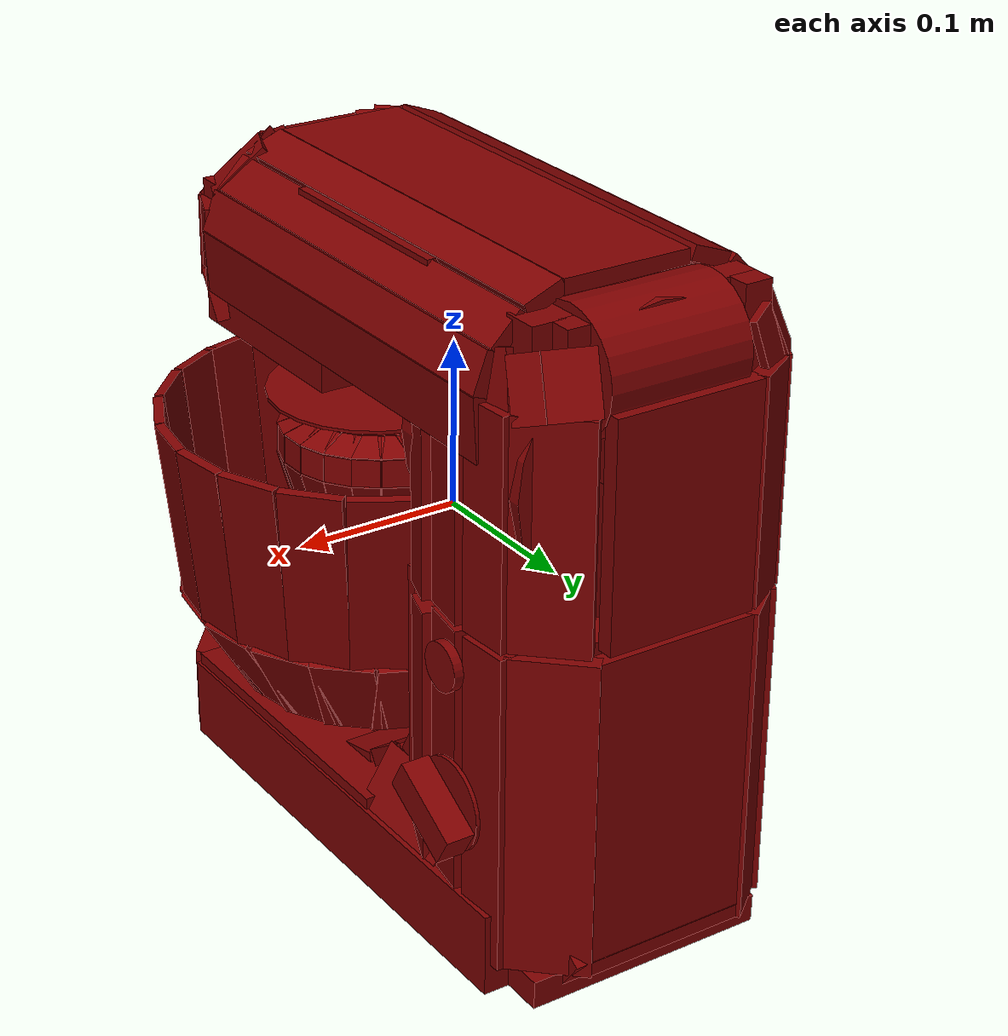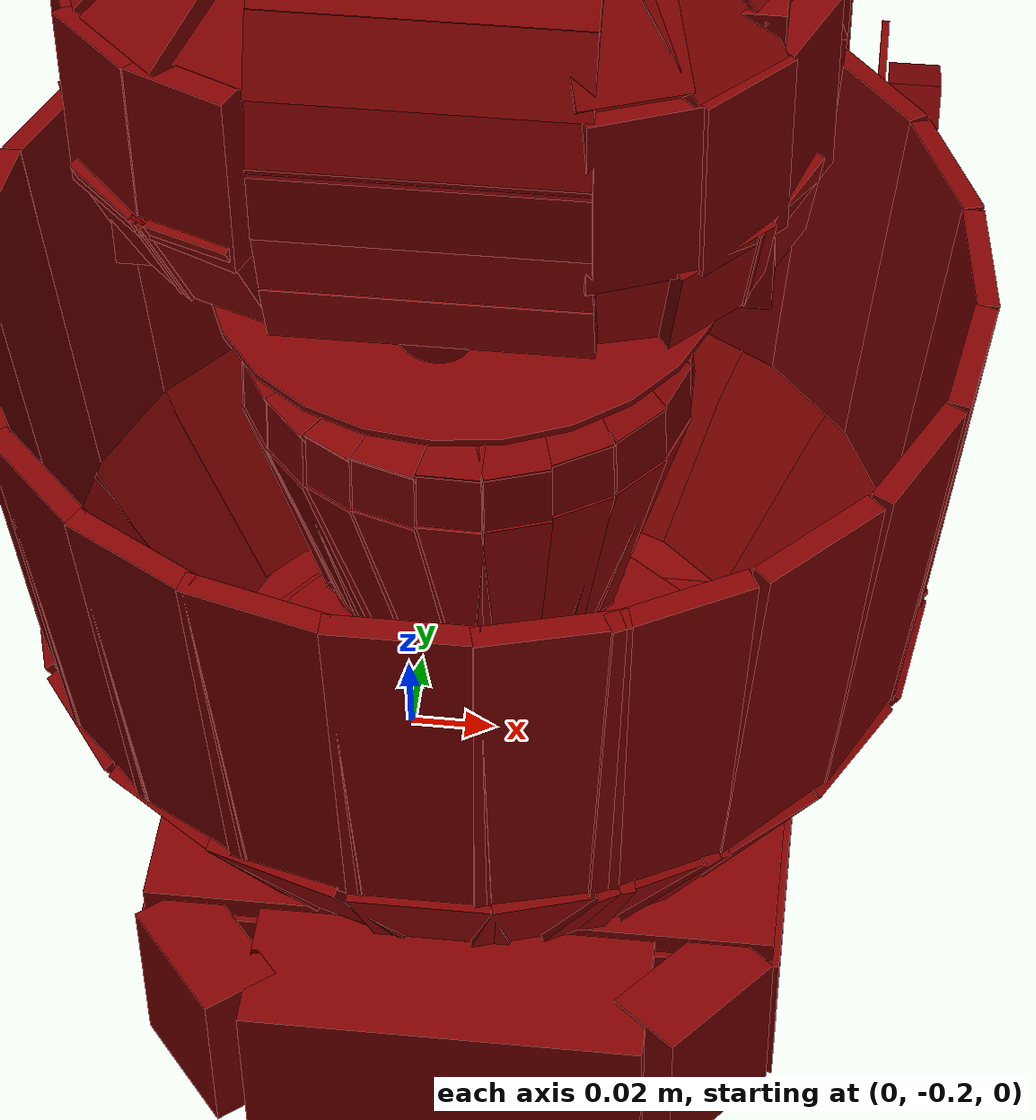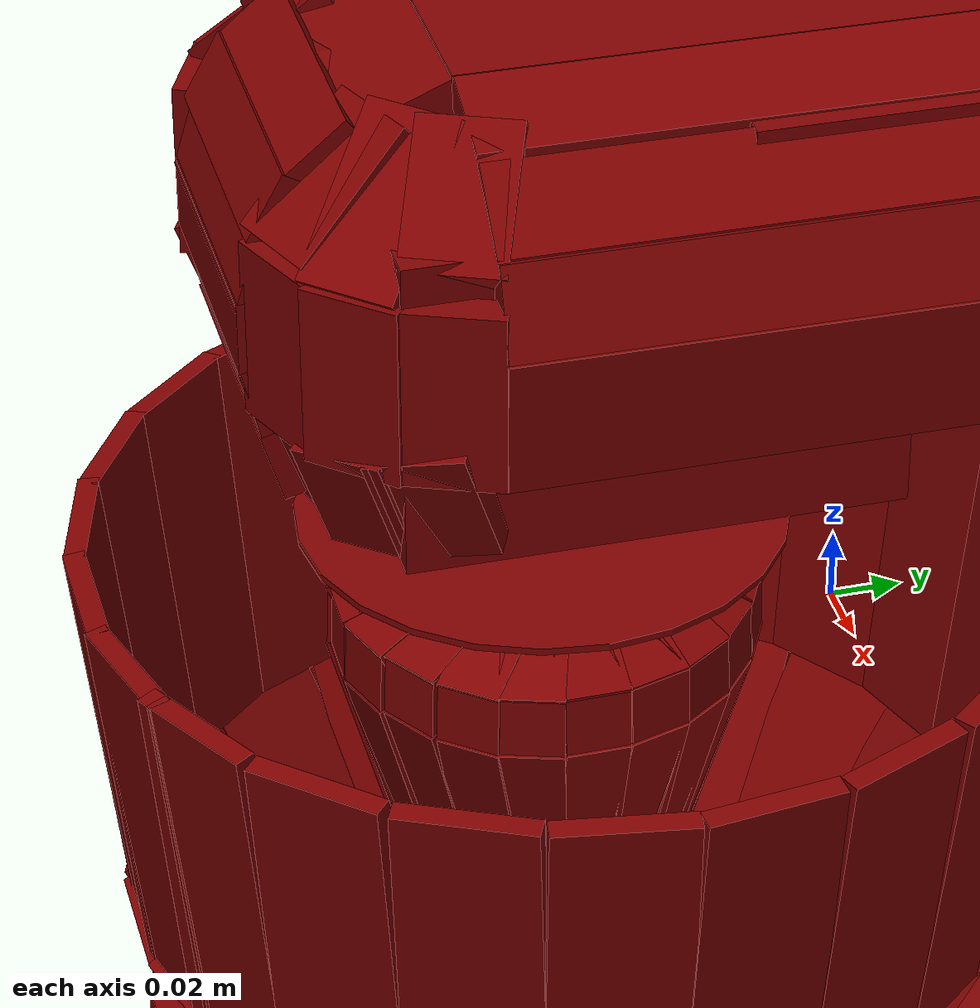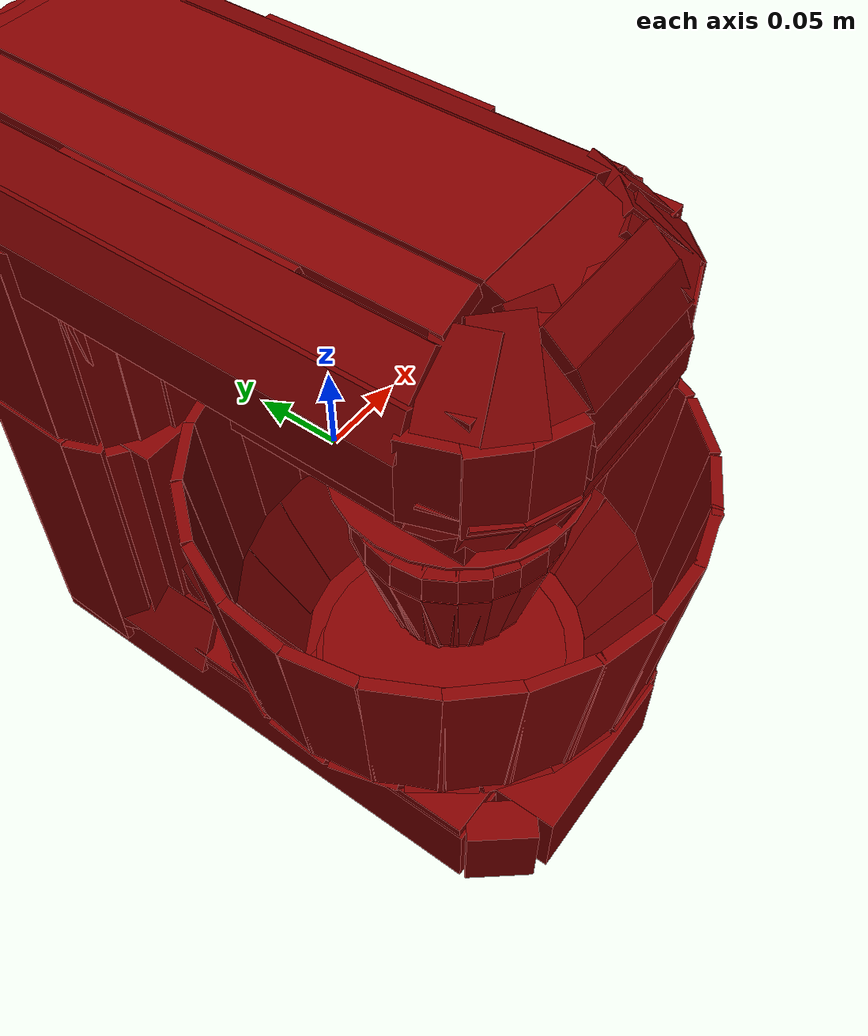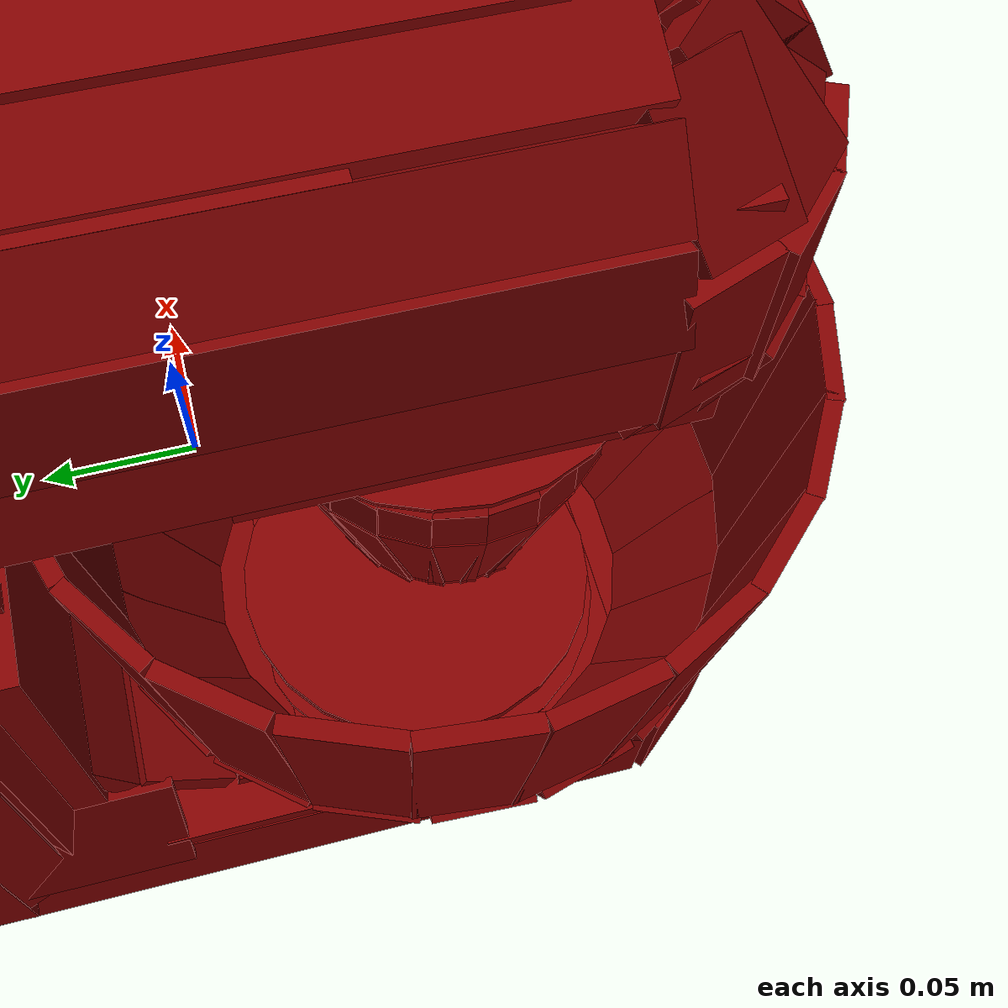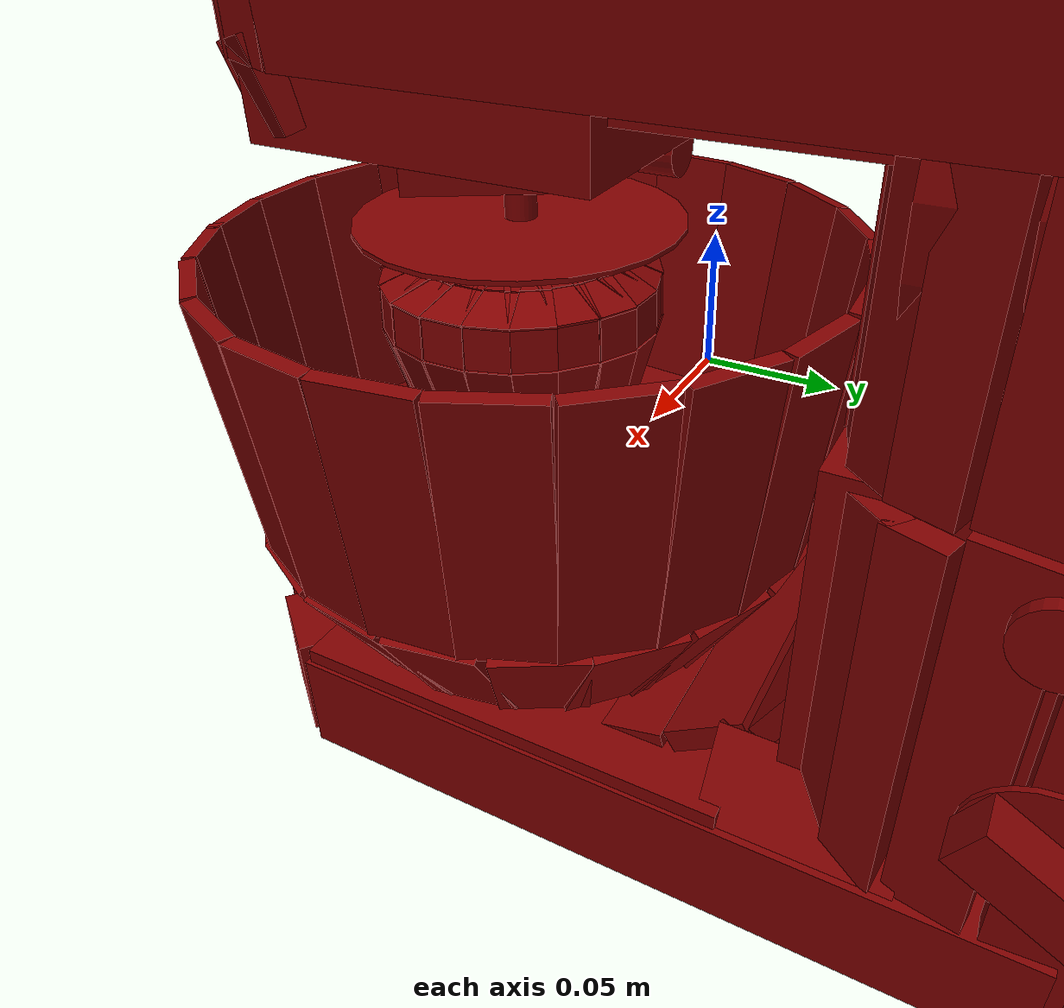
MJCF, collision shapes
<?xml version='1.0' encoding='UTF-8'?>
<mujoco model="model">
  <option timestep="0.002" gravity="0.0 0.0 -9.81"/>
  <compiler angle="radian"/>
  <asset>
    <mesh file="visuals/Blender001.obj" name="Blender001_vis"/>
    <mesh file="visuals/Body001.obj" name="Body001_vis"/>
    <mesh file="visuals/Button001.obj" name="Button001_vis"/>
    <mesh file="visuals/Container001.obj" name="Container001_vis"/>
    <mesh file="visuals/Knob001.obj" name="Knob001_vis"/>
    <mesh file="visuals/Lid001.obj" name="Lid001_vis"/>
    <texture file="visuals/T_BC001.png" name="Body001_material" type="2d"/>
    <material name="Body001_material" rgba="1 1 1 1.0" texture="Body001_material" shininess="0.1" specular="1"/>
    <texture file="visuals/T_BC001.png" name="Button001_material" type="2d"/>
    <material name="Button001_material" rgba="1 1 1 1.0" texture="Button001_material" shininess="0.4472135901451111" specular="0.3103448502657381"/>
    <texture file="visuals/T_BC001.png" name="Container001_material" type="2d"/>
    <material name="Container001_material" rgba="1 1 1 1.0" texture="Container001_material" shininess="0.1" specular="4"/>
    <texture file="visuals/T_BC001.png" name="Knob001_material" type="2d"/>
    <material name="Knob001_material" rgba="1 1 1 1.0" texture="Knob001_material" shininess="0.4472135901451111" specular="0.3103448502657381"/>
    <texture file="visuals/T_BC001.png" name="Lid001_material" type="2d"/>
    <material name="Lid001_material" rgba="1 1 1 1.0" texture="Lid001_material" shininess="0.1" specular="1"/>
    <texture file="visuals/T_BC001.png" name="Blender001_material" type="2d"/>
    <material name="Blender001_material" rgba="1 1 1 1.0" texture="Blender001_material" shininess="0.1" specular="4"/>
  </asset>
  <default>
    <default class="visual">
      <geom conaffinity="0" contype="0" group="1" type="mesh"/>
    </default>
    <default class="collision">
      <geom group="0" rgba="0.5 0 0 0.5"/>
    </default>
    <default class="spawn">
      <geom group="0" rgba="1 1 1 0.5" contype="0" conaffinity="0"/>
      <site group="0" rgba="1 1 1 0.5"/>
    </default>
    <default class="region">
      <geom group="1" conaffinity="0" contype="0" rgba="0 1 0 0"/>
    </default>
  </default>
  <worldbody>
    <body>
      <body name="object">
        <geom mesh="Body001_vis" type="mesh" solimp="0.998 0.998 0.001" solref="0.001 1" friction="0.95 0.3 0.1" class="visual" material="Body001_material"/>
        <geom class="collision" type="box" pos="0.001627 0.010409 -0.172537" size="0.0899050235748291 0.16075736284255981 0.024705523625016212" quat="1.0 0.0 0.0 0.0"/>
        <geom class="collision" type="cylinder" pos="-0.006757 -0.073994 -0.141833" size="0.07319789379835129 0.002024284331128001" quat="1.0 0.0 0.0 0.0"/>
        <geom class="collision" type="box" pos="0.002793 0.193195 -0.177576" size="0.055442556738853455 0.00843463372439146 0.014128785580396652" quat="0.9534308910369873 -0.30161160230636597 6.697122907492269e-17 1.2026518188257233e-23"/>
        <geom class="collision" type="box" pos="0.002793 0.181617 -0.188416" size="0.07363889366388321 0.00843463372439146 0.014128785580396652" quat="0.6979237198829651 -0.7161720991134644 1.5902215080597956e-16 7.135739925789815e-24"/>
        <geom class="collision" type="box" pos="-0.001636 0.202850 -0.084903" size="0.049669720232486725 0.005021312274038792 0.0946040004491806" quat="1.0 0.0 0.0 0.0"/>
        <geom class="collision" type="box" pos="-0.059046 0.196671 -0.084903" size="0.014814227819442749 0.005021312274038792 0.09460443258285522" quat="0.9436448812484741 0.0 0.0 0.3309597671031952"/>
        <geom class="collision" type="box" pos="-0.079113 0.177679 -0.084903" size="0.014814227819442749 0.005021311808377504 0.09460443258285522" quat="0.8611398339271545 0.0 0.0 0.5083681344985962"/>
        <geom class="collision" type="box" pos="-0.087493 0.136347 -0.084903" size="0.027245767414569855 0.00502131087705493 0.09460443258285522" quat="0.7145032286643982 0.0 0.0 0.6996321678161621"/>
        <geom class="collision" type="box" pos="0.083176 0.125754 -0.084903" size="0.014814227819442749 0.005021311808377504 0.09460443258285522" quat="0.6449642181396484 0.0 -0.0 -0.7642127871513367"/>
        <geom class="collision" type="box" pos="0.083588 0.160960 -0.084903" size="0.016015637665987015 0.005043074022978544 0.09460443258285522" quat="0.7272552847862244 0.0 -0.0 -0.6863670349121094"/>
        <geom class="collision" type="box" pos="0.063890 0.189000 -0.084903" size="0.02448882907629013 0.00502131087705493 0.09460443258285522" quat="0.9296313524246216 0.0 -0.0 -0.3684908449649811"/>
        <geom class="collision" type="box" pos="-0.001636 0.070119 -0.044186" size="0.04967014491558075 0.005021312274038792 0.05387219786643982" quat="1.0 0.0 0.0 0.0"/>
        <geom class="collision" type="box" pos="-0.001636 0.064846 -0.098851" size="0.06912857294082642 0.005021312274038792 0.019002310931682587" quat="0.9673065543174744 -0.25360992550849915 5.631270909715641e-17 8.218425880226234e-25"/>
        <geom class="collision" type="box" pos="-0.001636 0.035312 -0.126138" size="0.06912857294082642 0.005021312739700079 0.019002310931682587" quat="0.8780341148376465 -0.47859808802604675 1.0627014322595361e-16 1.9115638012270297e-23"/>
        <geom class="collision" type="box" pos="-0.001636 -0.001868 -0.144052" size="0.06912857294082642 0.005021311808377504 0.019002312794327736" quat="0.781984269618988 -0.623298168182373 1.3839999550455074e-16 2.208306610272578e-23"/>
        <geom class="collision" type="box" pos="-0.072515 0.081909 -0.077618" size="0.011155763640999794 0.005021311342716217 0.08598798513412476" quat="0.955824613571167 0.0 -0.0 -0.293937623500824"/>
        <geom class="collision" type="box" pos="-0.084344 0.100077 -0.077618" size="0.011155763640999794 0.00502131087705493 0.08598798513412476" quat="0.8310907483100891 0.0 -0.0 -0.5561368465423584"/>
        <geom class="collision" type="box" pos="-0.057290 0.074326 -0.077618" size="0.011155763640999794 0.005021311342716217 0.08598798513412476" quat="0.9927864670753479 0.0 -0.0 -0.11989592015743256"/>
        <geom class="collision" type="box" pos="0.072413 0.083304 -0.081032" size="0.011155763640999794 0.005021311342716217 0.08598798513412476" quat="0.9016786813735962 0.0 0.0 0.4324067234992981"/>
        <geom class="collision" type="box" pos="0.053360 0.072961 -0.081032" size="0.011155763640999794 0.005021311342716217 0.08598798513412476" quat="0.9878917932510376 0.0 0.0 0.1551445871591568"/>
        <geom class="collision" type="box" pos="0.081185 0.097877 -0.081032" size="0.011155763640999794 0.00502131087705493 0.08598798513412476" quat="0.8107764720916748 0.0 0.0 0.5853558778762817"/>
        <geom class="collision" type="box" pos="-0.080959 0.077803 -0.134793" size="0.02172514796257019 0.038140490651130676 0.0026141840498894453" quat="0.8441252112388611 0.0 -0.5361461043357849 0.0"/>
        <geom class="collision" type="box" pos="0.076827 0.077803 -0.134312" size="0.02172514796257019 0.038140490651130676 0.002614184282720089" quat="0.8749390244483948 0.0 0.48423314094543457 0.0"/>
        <geom class="collision" type="box" pos="0.001033 -0.050008 -0.146812" size="0.0886635109782219 0.09841278195381165 0.005824797321110964" quat="1.0 0.0 0.0 0.0"/>
        <geom class="collision" type="box" pos="0.001033 -0.167842 -0.169327" size="0.055596619844436646 0.01988396793603897 0.0256899893283844" quat="1.0 0.0 0.0 0.0"/>
        <geom class="collision" type="box" pos="-0.067666 -0.162509 -0.169327" size="0.011214721947908401 0.01988396793603897 0.0256899893283844" quat="0.9411333203315735 0.0 0.0 0.33803555369377136"/>
        <geom class="collision" type="box" pos="0.068767 -0.162509 -0.168235" size="0.011214721947908401 0.01988396793603897 0.0256899893283844" quat="0.33648473024368286 0.0 0.0 0.9416888952255249"/>
        <geom class="collision" type="box" pos="-0.001636 0.125866 -0.084903" size="0.07255306839942932 0.061715446412563324 0.09460416436195374" quat="1.0 0.0 0.0 0.0"/>
        <body name="Button001">
          <joint axis="-1.0 0.0 0.0" pos="0.096840 0.139957 -0.007721" limited="true" name="Button001_joint" range="0.0 0.0055000000000000005" type="slide" damping="1" frictionloss="1" armature=".01" stiffness="0.05"/>
          <geom mesh="Button001_vis" type="mesh" solimp="0.998 0.998 0.001" solref="0.001 1" friction="0.95 0.3 0.1" class="visual" material="Button001_material"/>
          <geom class="collision" type="cylinder" pos="0.096962 0.139857 -0.007832" size="0.013906983658671379 0.0027774162590503693" quat="0.7071068286895752 -0.0 0.7071067690849304 0.0"/>
        </body>
        <body name="Container001">
          <joint axis="0.0 0.0 1.0" pos="-0.000000 -0.076861 -0.050777" limited="true" name="Container001_joint" range="0.0 0.05" type="slide" damping="1" frictionloss="1" armature=".01" stiffness="0.05"/>
          <geom mesh="Container001_vis" type="mesh" solimp="0.998 0.998 0.001" solref="0.001 1" friction="0.95 0.3 0.1" class="visual" material="Container001_material"/>
          <geom class="collision" type="box" pos="-0.001055 -0.198964 -0.018802" size="0.018773013725876808 0.0029905198607593775 0.05602985620498657" quat="0.9985294938087463 0.0542115792632103 0.0 0.0"/>
          <geom class="collision" type="box" pos="-0.034630 -0.194074 -0.018805" size="0.018773015588521957 0.002990520093590021 0.05602986365556717" quat="0.9891883730888367 0.053704436868429184 -0.007397890090942383 -0.13626262545585632"/>
          <geom class="collision" type="box" pos="-0.064896 -0.180769 -0.018810" size="0.018773013725876808 0.0029905205592513084 0.056029871106147766" quat="0.9622957706451416 0.05224435776472092 -0.01447127666324377 -0.266548216342926"/>
          <geom class="collision" type="box" pos="-0.091271 -0.159260 -0.018817" size="0.018773017451167107 0.002990520093590021 0.05602985620498657" quat="0.9167933464050293 0.04977397248148918 -0.021481214091181755 -0.39566531777381897"/>
          <geom class="collision" type="box" pos="-0.110821 -0.131465 -0.018826" size="0.01877301000058651 0.002990520093590021 0.05602986365556717" quat="0.8542089462280273 0.04637617990374565 -0.02807384729385376 -0.5170959234237671"/>
          <geom class="collision" type="box" pos="-0.122505 -0.097562 -0.018836" size="0.01877301000058651 0.002990520792081952 0.056029871106147766" quat="0.7708883881568909 0.041852597147226334 -0.0344565212726593 -0.6346591114997864"/>
          <geom class="collision" type="box" pos="-0.124060 -0.061802 -0.018847" size="0.01877301000058651 0.0029905198607593775 0.056029871106147766" quat="0.6717950701713562 0.036472681909799576 -0.04010780155658722 -0.7387506365776062"/>
          <geom class="collision" type="box" pos="-0.115470 -0.027275 -0.018857" size="0.01877300813794136 0.002990520093590021 0.05602985620498657" quat="0.5595933794975281 0.030381105840206146 -0.044898562133312225 -0.8269923329353333"/>
          <geom class="collision" type="box" pos="-0.096779 0.004284 -0.018866" size="0.018773013725876808 0.0029905198607593775 0.05602985620498657" quat="0.4320467412471771 0.02345641888678074 -0.04887421429157257 -0.9002203941345215"/>
          <geom class="collision" type="box" pos="-0.069893 0.028914 -0.018872" size="0.01877301000058651 0.002990520093590021 0.05602985620498657" quat="0.2960401773452759 0.016072440892457962 -0.05177425965666771 -0.9536358714103699"/>
          <geom class="collision" type="box" pos="-0.038024 0.044395 -0.018875" size="0.018773013725876808 0.0029905205592513084 0.056029871106147766" quat="0.15786147117614746 0.008570518344640732 -0.053529784083366394 -0.9859720468521118"/>
          <geom class="collision" type="box" pos="-0.003863 0.050264 -0.018876" size="0.01877300813794136 0.0029905198607593775 0.05602985620498657" quat="0.01961621083319187 0.0010649911127984524 -0.05420108139514923 -0.9983367919921875"/>
          <geom class="collision" type="box" pos="0.033348 0.045766 -0.018873" size="0.018773013725876808 0.002990520093590021 0.05602986365556717" quat="0.13031423091888428 0.007074950262904167 0.05374795198440552 0.9899895191192627"/>
          <geom class="collision" type="box" pos="0.066796 0.030885 -0.018868" size="0.01877301000058651 0.0029905205592513084 0.05602986365556717" quat="0.2739492654800415 0.014873085543513298 0.05213141068816185 0.9602150321006775"/>
          <geom class="collision" type="box" pos="0.094664 0.006712 -0.018859" size="0.018773013725876808 0.002990520792081952 0.05602986365556717" quat="0.4127850830554962 0.02241067960858345 0.04936249181628227 0.9092137217521667"/>
          <geom class="collision" type="box" pos="0.114189 -0.024453 -0.018850" size="0.01877300813794136 0.002990518929436803 0.05602985620498657" quat="0.5422492623329163 0.029439471662044525 0.04552154615521431 0.8384669423103333"/>
          <geom class="collision" type="box" pos="0.123710 -0.059450 -0.018839" size="0.01877301000058651 0.002990519627928734 0.05602985620498657" quat="0.6584212779998779 0.03574661910533905 0.04075627774000168 0.7506946921348572"/>
          <geom class="collision" type="box" pos="0.122827 -0.095275 -0.018828" size="0.01877300813794136 0.002990520792081952 0.05602985620498657" quat="0.7595313787460327 0.041236039251089096 0.03519212454557419 0.6482077240943909"/>
          <geom class="collision" type="box" pos="0.111427 -0.130094 -0.018818" size="0.018773017451167107 0.002990520093590021 0.056029871106147766" quat="0.8466377854347229 0.04596516862511635 0.028741935268044472 0.5294011235237122"/>
          <geom class="collision" type="box" pos="0.089911 -0.160603 -0.018810" size="0.018773013725876808 0.00299051939509809 0.05602986365556717" quat="0.9164795279502869 0.04975699633359909 0.021520676091313362 0.39639171957969666"/>
          <geom class="collision" type="box" pos="0.060288 -0.183393 -0.018804" size="0.018773013725876808 0.002990520792081952 0.056029871106147766" quat="0.9656398892402649 0.05242596194148064 0.013799061067402363 0.2541666626930237"/>
          <geom class="collision" type="box" pos="0.032276 -0.194704 -0.018802" size="0.018773015588521957 0.002990520093590021 0.056029871106147766" quat="0.9893670678138733 0.05371414124965668 0.007327110506594181 0.1349589079618454"/>
          <geom class="collision" type="box" pos="-0.001055 -0.177372 -0.102902" size="0.018773015588521957 0.0027088394854217768 0.034455206245183945" quat="0.9623625874519348 0.271768718957901 0.0 0.0"/>
          <geom class="collision" type="box" pos="-0.034210 -0.171531 -0.102936" size="0.018773017451167107 0.002708839252591133 0.03447578847408295" quat="0.9493533968925476 0.2680949568748474 -0.04453460872173309 -0.15770187973976135"/>
          <geom class="collision" type="box" pos="-0.061168 -0.157054 -0.103222" size="0.018773015588521957 0.0027088394854217768 0.0347813256084919" quat="0.9152575135231018 0.25846636295318604 -0.08398435264825821 -0.29739782214164734"/>
          <geom class="collision" type="box" pos="-0.084176 -0.133348 -0.103362" size="0.018773015588521957 0.002708839252591133 0.034901391714811325" quat="0.8554472923278809 0.24157610535621643 -0.12449585646390915 -0.4408533573150635"/>
          <geom class="collision" type="box" pos="-0.098740 -0.102602 -0.103520" size="0.018773015588521957 0.002708838786929846 0.03503530099987984" quat="0.7705292701721191 0.21759547293186188 -0.1628202646970749 -0.576564371585846"/>
          <geom class="collision" type="box" pos="-0.102357 -0.069602 -0.103903" size="0.018773015588521957 0.002708838554099202 0.035432346165180206" quat="0.667048454284668 0.18837277591228485 -0.19589264690876007 -0.6936772465705872"/>
          <geom class="collision" type="box" pos="-0.095013 -0.035996 -0.103898" size="0.01877301000058651 0.002708838554099202 0.03537725284695625" quat="0.541220486164093 0.15283925831317902 -0.22471848130226135 -0.7957525849342346"/>
          <geom class="collision" type="box" pos="-0.078269 -0.007970 -0.103609" size="0.018773015588521957 0.002708838786929846 0.03499946743249893" quat="0.407856822013855 0.1151777133345604 -0.24615508317947388 -0.8716619610786438"/>
          <geom class="collision" type="box" pos="-0.052433 0.013678 -0.103852" size="0.018773015588521957 0.002708838554099202 0.03525856137275696" quat="0.25940626859664917 0.07325565069913864 -0.26170945167541504 -0.9267417192459106"/>
          <geom class="collision" type="box" pos="-0.021732 0.026193 -0.103160" size="0.018773015588521957 0.002708838088437915 0.034437429159879684" quat="0.10678956657648087 0.03015710599720478 -0.2700902223587036 -0.9564192891120911"/>
          <geom class="collision" type="box" pos="0.011454 0.027834 -0.103194" size="0.018773015588521957 0.002708839951083064 0.03448551520705223" quat="0.04864132031798363 0.01373619120568037 0.27142131328582764 0.9611325860023499"/>
          <geom class="collision" type="box" pos="0.043581 0.018683 -0.103308" size="0.018773017451167107 0.0027088397182524204 0.034642696380615234" quat="0.20373256504535675 0.057533543556928635 0.2656089663505554 0.9405502676963806"/>
          <geom class="collision" type="box" pos="0.070956 -0.000027 -0.103251" size="0.01877301186323166 0.002708839252591133 0.03461287543177605" quat="0.3524662256240845 0.09953554719686508 0.252885103225708 0.8954939246177673"/>
          <geom class="collision" type="box" pos="0.090202 -0.024981 -0.103116" size="0.01877300813794136 0.0027088383212685585 0.034498170018196106" quat="0.48533061146736145 0.13705609738826752 0.23467819392681122 0.8310210704803467"/>
          <geom class="collision" type="box" pos="0.101641 -0.057595 -0.102809" size="0.01877301186323166 0.002708839252591133 0.03419177606701851" quat="0.617851197719574 0.17447955906391144 0.20836293697357178 0.7378358244895935"/>
          <geom class="collision" type="box" pos="0.101890 -0.090980 -0.102445" size="0.018773015588521957 0.0027088394854217768 0.033816687762737274" quat="0.7291343212127686 0.20590564608573914 0.1773727536201477 0.6280962824821472"/>
          <geom class="collision" type="box" pos="0.090734 -0.123954 -0.102185" size="0.01877301186323166 0.002708839252591133 0.03355877473950386" quat="0.8245988488197327 0.23286457359790802 0.1401153802871704 0.49616381525993347"/>
          <geom class="collision" type="box" pos="0.071331 -0.149202 -0.102225" size="0.018773017451167107 0.0027088394854217768 0.03363889455795288" quat="0.8912619352340698 0.25169000029563904 0.10251995921134949 0.3630344271659851"/>
          <geom class="collision" type="box" pos="0.030032 -0.172963 -0.102778" size="0.018773017451167107 0.002708839252591133 0.034312114119529724" quat="0.9510646462440491 0.2685782015323639 0.04152083024382591 0.1470297873020172"/>
          <geom class="collision" type="box" pos="0.050932 -0.164040 -0.102661" size="0.01877300813794136 0.002708838554099202 0.034167684614658356" quat="0.9289951920509338 0.26234591007232666 0.07094284892082214 0.25121641159057617"/>
          <geom class="collision" type="cylinder" pos="0.000690 -0.073994 -0.135635" size="0.07319789379835129 0.002024284331128001" quat="1.0 0.0 0.0 0.0"/>
        </body>
        <body name="Knob001">
          <joint axis="-1.0 0.0 0.0" pos="0.105461 0.152281 -0.082076" limited="true" name="Knob001_joint" range="0.0 4.886921905584122" type="hinge" damping="0.05" armature="0.001"/>
          <geom mesh="Knob001_vis" type="mesh" solimp="0.998 0.998 0.001" solref="0.001 1" friction="0.95 0.3 0.1" class="visual" material="Knob001_material"/>
          <geom class="collision" type="cylinder" pos="0.101475 0.152629 -0.082106" size="0.026152539998292923 0.0011611760128289461" quat="0.4999983608722687 0.5000000596046448 -0.5000016093254089 -0.4999999403953552"/>
          <geom class="collision" type="box" pos="0.112086 0.152281 -0.082076" size="0.008335120044648647 0.024997124448418617 0.00985212903469801" quat="0.96536785364151 -0.26089251041412354 -5.792977440280368e-17 -4.785050390784267e-24"/>
        </body>
        <body name="Lid001">
          <joint axis="-1.0 0.0 0.0" pos="0.005768 0.210196 0.013512" limited="true" name="Lid001_joint" range="0.0 1.5707963267948966" type="hinge" damping="1" frictionloss="1" armature=".01" stiffness="0.05"/>
          <geom mesh="Lid001_vis" type="mesh" solimp="0.998 0.998 0.001" solref="0.001 1" friction="0.95 0.3 0.1" class="visual" material="Lid001_material"/>
          <geom class="collision" type="cylinder" pos="0.000565 -0.081149 0.078593" size="0.009613879956305027 0.06693771481513977" quat="0.49999919533729553 -0.5000008344650269 -0.49999916553497314 -0.5000007748603821"/>
          <geom class="collision" type="box" pos="0.007999 -0.093756 0.062652" size="0.029878204688429832 0.014719265513122082 0.005266072228550911" quat="0.8704594373703003 -7.596937479092958e-08 2.9401514112237237e-08 -0.49224016070365906"/>
          <geom class="collision" type="box" pos="-0.001636 0.203706 0.078061" size="0.04505397379398346 0.005021312274038792 0.06495030224323273" quat="1.0 0.0 0.0 0.0"/>
          <geom class="collision" type="box" pos="-0.059077 0.196709 0.078061" size="0.014814228750765324 0.005021311342716217 0.06495030224323273" quat="0.9627028703689575 0.0 0.0 0.2705608606338501"/>
          <geom class="collision" type="box" pos="-0.079113 0.177679 0.078061" size="0.014814227819442749 0.005021311342716217 0.06495030224323273" quat="0.8611398339271545 0.0 0.0 0.5083681344985962"/>
          <geom class="collision" type="box" pos="-0.087493 0.136347 0.078061" size="0.027245767414569855 0.00502131087705493 0.06495030224323273" quat="0.7145032286643982 0.0 0.0 0.6996321678161621"/>
          <geom class="collision" type="box" pos="0.083176 0.125754 0.078061" size="0.014814227819442749 0.005021311808377504 0.06495030224323273" quat="0.6449642181396484 0.0 -0.0 -0.7642127871513367"/>
          <geom class="collision" type="box" pos="0.083588 0.160960 0.078061" size="0.016015637665987015 0.005043073557317257 0.06495030224323273" quat="0.7272552847862244 0.0 -0.0 -0.6863670349121094"/>
          <geom class="collision" type="box" pos="0.066898 0.186603 0.078061" size="0.023743215948343277 0.00502131087705493 0.06495030224323273" quat="0.9296313524246216 0.0 -0.0 -0.3684908449649811"/>
          <geom class="collision" type="box" pos="-0.001636 0.070119 0.076215" size="0.049669720232486725 0.005021312274038792 0.06262287497520447" quat="1.0 0.0 0.0 0.0"/>
          <geom class="collision" type="box" pos="-0.072515 0.081909 0.076421" size="0.011155763640999794 0.005021311808377504 0.061475761234760284" quat="0.955824613571167 0.0 -0.0 -0.293937623500824"/>
          <geom class="collision" type="box" pos="-0.084344 0.100077 0.076421" size="0.011155763640999794 0.00502131087705493 0.061475761234760284" quat="0.8310907483100891 0.0 -0.0 -0.5561368465423584"/>
          <geom class="collision" type="box" pos="-0.057290 0.074326 0.076421" size="0.011155763640999794 0.005021311342716217 0.061475761234760284" quat="0.9927864670753479 0.0 -0.0 -0.11989592015743256"/>
          <geom class="collision" type="box" pos="0.072413 0.083304 0.073980" size="0.011155763640999794 0.005021311342716217 0.061475761234760284" quat="0.9016786813735962 0.0 0.0 0.4324067234992981"/>
          <geom class="collision" type="box" pos="0.053360 0.072961 0.073980" size="0.011155763640999794 0.005021311808377504 0.061475761234760284" quat="0.9878917932510376 0.0 0.0 0.1551445871591568"/>
          <geom class="collision" type="box" pos="0.081185 0.097877 0.073980" size="0.011155763640999794 0.00502131087705493 0.061475761234760284" quat="0.8107764720916748 0.0 0.0 0.5853558778762817"/>
          <geom class="collision" type="cylinder" pos="0.000235 0.132521 0.098540" size="0.08380713313817978 0.05254381522536278" quat="0.7071067094802856 0.7071068286895752 0.0 0.0"/>
          <geom class="collision" type="cylinder" pos="0.001456 0.022621 0.136040" size="0.05096551775932312 0.16331139206886292" quat="0.7071067094802856 0.7071068286895752 0.0 0.0"/>
          <geom class="collision" type="box" pos="0.001414 0.021183 0.192345" size="0.03828424587845802 0.13630065321922302 0.004347546491771936" quat="1.0 0.0 0.0 0.0"/>
          <geom class="collision" type="box" pos="0.050233 0.021183 0.188491" size="0.011963212862610817 0.13630065321922302 0.004347546026110649" quat="0.9812838435173035 4.2135749252371736e-16 0.1925669014453888 2.5873070796933462e-08"/>
          <geom class="collision" type="box" pos="0.070255 0.021183 0.175274" size="0.011963212862610817 0.13630065321922302 0.004347546026110649" quat="0.9243265986442566 -4.5678115153172105e-15 0.38160234689712524 5.1271651813067365e-08"/>
          <geom class="collision" type="box" pos="0.083759 0.021183 0.157144" size="0.011963211931288242 0.13630065321922302 0.004347546026110649" quat="0.8209965229034424 -7.004454677541185e-15 0.5709332227706909 7.67099450627029e-08"/>
          <geom class="collision" type="box" pos="0.086447 0.021183 0.128866" size="0.01816057227551937 0.13630065321922302 0.004347546026110649" quat="0.684807300567627 -2.1998922683508226e-09 0.7287241816520691 9.574494441721981e-08"/>
          <geom class="collision" type="box" pos="-0.084984 0.021183 0.156054" size="0.011963212862610817 0.13630065321922302 0.004347546026110649" quat="0.8300378322601318 2.5845179623973933e-15 -0.5577071309089661 -7.493287057513953e-08"/>
          <geom class="collision" type="box" pos="-0.071767 0.021183 0.176076" size="0.011963212862610817 0.13630065321922302 0.004347546026110649" quat="0.9234311580657959 -7.019975709266673e-15 -0.3837641179561615 -5.15621039198777e-08"/>
          <geom class="collision" type="box" pos="-0.050307 0.021183 0.189359" size="0.011963212862610817 0.13630065321922302 0.004347546026110649" quat="0.9842429161071777 -1.7078779525597082e-14 -0.17682145535945892 -2.3757507960908697e-08"/>
          <geom class="collision" type="box" pos="-0.086185 0.021183 0.130157" size="0.004447567276656628 0.13630065321922302 0.017324483022093773" quat="1.0 0.0 0.0 0.0"/>
          <geom class="collision" type="cylinder" pos="0.001456 0.168747 0.153610" size="0.03575201332569122 0.042757969349622726" quat="0.4999999701976776 0.5 0.5 0.5"/>
          <geom class="collision" type="box" pos="-0.080979 0.164343 0.160095" size="0.017529677599668503 0.014469706453382969 0.0016807245556265116" quat="0.8362656235694885 -0.09358292073011398 -0.536928117275238 -0.06008543074131012"/>
          <geom class="collision" type="box" pos="-0.073522 0.183324 0.156681" size="0.01752968318760395 0.00930290948599577 0.002278650412335992" quat="0.7895967364311218 -0.29092079401016235 -0.5069642066955566 -0.18678711354732513"/>
          <geom class="collision" type="box" pos="-0.058473 0.194119 0.154808" size="0.017529679462313652 0.00930290948599577 0.002278650412335992" quat="0.6993736028671265 -0.409210205078125 -0.49341464042663574 -0.3161732852458954"/>
          <geom class="collision" type="box" pos="0.059337 0.191780 0.158281" size="0.017529677599668503 0.014469705522060394 0.0016807245556265116" quat="0.4333280324935913 -0.492570161819458 -0.2332899570465088 -0.7177584767341614"/>
          <geom class="collision" type="box" pos="0.074730 0.178404 0.154868" size="0.0175296813249588 0.00930290948599577 0.002278650412335992" quat="0.30291128158569336 -0.5819306969642639 -0.05481088161468506 -0.7527264952659607"/>
          <geom class="collision" type="box" pos="0.079871 0.160612 0.152994" size="0.0175296813249588 0.00930290948599577 0.002278650412335992" quat="0.14517684280872345 -0.6390992403030396 0.049629367887973785 -0.7536662220954895"/>
          <geom class="collision" type="box" pos="0.055156 0.162825 0.155201" size="0.014362861402332783 0.010855750180780888 0.02878350391983986" quat="1.0 0.0 0.0 0.0"/>
          <geom class="collision" type="box" pos="0.049210 0.179202 0.155201" size="0.008402454666793346 0.006780486553907394 0.02878350391983986" quat="1.0 0.0 0.0 0.0"/>
          <geom class="collision" type="box" pos="-0.052252 0.162825 0.155201" size="0.014362861402332783 0.010855750180780888 0.02878350391983986" quat="1.0 0.0 0.0 0.0"/>
          <geom class="collision" type="box" pos="-0.058198 0.179202 0.155201" size="0.00840245932340622 0.006780486553907394 0.02878350391983986" quat="1.0 0.0 0.0 0.0"/>
          <geom class="collision" type="box" pos="0.001033 -0.073571 0.126599" size="0.07779024541378021 0.06399105489253998 0.04254274070262909" quat="1.0 0.0 0.0 0.0"/>
          <geom class="collision" type="box" pos="0.001033 0.015672 0.144537" size="0.06687738746404648 0.06399117410182953 0.04254274070262909" quat="1.0 0.0 0.0 0.0"/>
          <geom class="collision" type="box" pos="0.001414 -0.119442 0.172871" size="0.03828424587845802 0.013255536556243896 0.019374029710888863" quat="0.9806175231933594 0.19593189656734467 -4.3505620565508144e-17 2.6379463311088585e-24"/>
          <geom class="collision" type="box" pos="0.001414 -0.136520 0.167822" size="0.03828424587845802 0.009861667640507221 0.018606586381793022" quat="0.9398419260978699 0.3416096866130829 -7.585258790256575e-17 -8.535439495750613e-25"/>
          <geom class="collision" type="box" pos="0.001414 -0.145517 0.158643" size="0.03828424587845802 0.009861668571829796 0.018154846504330635" quat="0.8608698844909668 0.5088251829147339 -1.1298188671620888e-16 -3.3041172774626567e-24"/>
          <geom class="collision" type="box" pos="0.001414 -0.151445 0.144798" size="0.03828424587845802 0.009861668571829796 0.01588960364460945" quat="0.8030709624290466 0.5958834290504456 -1.323127005848791e-16 -4.366051654141558e-24"/>
          <geom class="collision" type="box" pos="0.001414 -0.153333 0.132063" size="0.03828424587845802 0.015890277922153473 0.009990944527089596" quat="1.0 0.0 0.0 0.0"/>
          <geom class="collision" type="box" pos="0.001414 -0.152777 0.116200" size="0.03828424587845802 0.009861668571829796 0.01418495923280716" quat="0.6199234127998352 0.7846623063087463 -1.7423003180388948e-16 -1.4786541336094722e-23"/>
          <geom class="collision" type="box" pos="0.001414 -0.147551 0.098043" size="0.03828424587845802 0.009861668571829796 0.01495105866342783" quat="0.5950084328651428 0.8037194609642029 -1.7846158341524535e-16 -2.403919502307146e-23"/>
          <geom class="collision" type="box" pos="-0.082621 -0.124118 0.134971" size="0.013216618448495865 0.00464509567245841 0.023897482082247734" quat="0.8223839998245239 0.0 -0.0 -0.568932831287384"/>
          <geom class="collision" type="box" pos="-0.071230 -0.145733 0.134971" size="0.01321661751717329 0.00464509567245841 0.023897482082247734" quat="0.9277811050415039 0.0 -0.0 -0.373124897480011"/>
          <geom class="collision" type="box" pos="-0.051060 -0.158965 0.134971" size="0.013216618448495865 0.00464509567245841 0.023897482082247734" quat="0.9782099723815918 0.0 -0.0 -0.20761796832084656"/>
          <geom class="collision" type="box" pos="0.048739 -0.158486 0.134971" size="0.01321661751717329 0.00464509567245841 0.023897482082247734" quat="0.9818600416183472 0.0 0.0 0.18960721790790558"/>
          <geom class="collision" type="box" pos="0.069250 -0.145852 0.134971" size="0.01321661751717329 0.00464509567245841 0.023897482082247734" quat="0.9156820178031921 0.0 0.0 0.40190356969833374"/>
          <geom class="collision" type="box" pos="0.081229 -0.125490 0.134971" size="0.01321661751717329 0.00464509567245841 0.023897482082247734" quat="0.8326998949050903 0.0 0.0 0.5537245273590088"/>
          <geom class="collision" type="box" pos="-0.065713 -0.124111 0.173061" size="0.01321661751717329 0.00464509567245841 0.020833054557442665" quat="0.754522979259491 -0.32712462544441223 0.22630779445171356 -0.5219858884811401"/>
          <geom class="collision" type="box" pos="-0.053272 -0.137049 0.173052" size="0.01321661751717329 0.00464509567245841 0.023897482082247734" quat="0.8512229919433594 -0.3690491318702698 0.14842009544372559 -0.3423355221748352"/>
          <geom class="collision" type="box" pos="-0.035374 -0.142221 0.172894" size="0.010962706990540028 0.004645095206797123 0.023897482082247734" quat="0.8974906206130981 -0.38910841941833496 0.0825854241847992 -0.190485879778862"/>
          <geom class="collision" type="box" pos="0.041923 -0.145028 0.172845" size="0.01321661751717329 0.004645096138119698 0.020546825602650642" quat="0.9025411605834961 -0.39129820466041565 -0.07149488478899002 0.1649051159620285"/>
          <geom class="collision" type="box" pos="0.055786 -0.135159 0.172959" size="0.01321661751717329 0.00464509567245841 0.023897482082247734" quat="0.8437832593917847 -0.3658235967159271 -0.15620142221450806 0.3602833151817322"/>
          <geom class="collision" type="box" pos="0.064229 -0.118746 0.176665" size="0.013216616585850716 0.004645094741135836 0.019503479823470116" quat="0.7690514922142029 -0.3334234356880188 -0.21692053973674774 0.5003339648246765"/>
          <geom class="collision" type="box" pos="-0.076672 -0.126327 0.107229" size="0.01321661937981844 0.00464509567245841 0.0175640769302845" quat="0.808824896812439 0.20893988013267517 0.015132883563637733 -0.5494701266288757"/>
          <geom class="collision" type="box" pos="-0.067012 -0.143185 0.102848" size="0.013216616585850716 0.00464509567245841 0.01756407879292965" quat="0.9102560877799988 0.20711825788021088 -0.03141559287905693 -0.3571399748325348"/>
          <geom class="collision" type="box" pos="-0.049561 -0.154090 0.102533" size="0.013216618448495865 0.00464509567245841 0.01756407506763935" quat="0.9581919312477112 0.19860298931598663 -0.06664641946554184 -0.19489312171936035"/>
          <geom class="collision" type="box" pos="0.047188 -0.151420 0.099723" size="0.013216620311141014 0.004645096138119698 0.015986895188689232" quat="0.9753819704055786 0.16564033925533295 0.03299707546830177 0.14179013669490814"/>
          <geom class="collision" type="box" pos="0.064559 -0.144467 0.099986" size="0.013216618448495865 0.004645096138119698 0.01598690077662468" quat="0.9199314117431641 0.1688370257616043 -0.004424192477017641 0.35383716225624084"/>
          <geom class="collision" type="box" pos="0.076643 -0.129413 0.103568" size="0.013216614723205566 0.004645096138119698 0.015986895188689232" quat="0.8451710343360901 0.16554726660251617 -0.03346046805381775 0.5071098804473877"/>
          <body name="Blender001">
            <joint axis="0.0 0.0 1.0" pos="-0.001016 -0.082096 -0.000655" limited="false" name="Blender001_joint" range="0 360" type="hinge" damping="1" frictionloss="1" armature=".01" stiffness="0.05"/>
            <geom mesh="Blender001_vis" type="mesh" solimp="0.998 0.998 0.001" solref="0.001 1" friction="0.95 0.3 0.1" class="visual" material="Blender001_material"/>
            <geom class="collision" type="cylinder" pos="-0.000770 -0.082110 0.040336" size="0.00644986005499959 0.013895629905164242" quat="1.0 0.0 0.0 0.0"/>
            <geom class="collision" type="cylinder" pos="-0.000770 -0.082110 0.042654" size="0.06606562435626984 0.0009801468113437295" quat="1.0 0.0 0.0 0.0"/>
            <geom class="collision" type="box" pos="0.045100 -0.096633 -0.028393" size="0.0020608543418347836 0.008796794340014458 0.034217726439237595" quat="0.9778345823287964 0.021900562569499016 0.13528378307819366 -0.15829776227474213"/>
            <geom class="collision" type="box" pos="0.031192 -0.092009 -0.067538" size="0.00206085410900414 0.008796795271337032 0.00875120423734188" quat="0.913358211517334 0.06062386929988861 0.374485045671463 -0.14785979688167572"/>
            <geom class="collision" type="box" pos="0.019093 -0.087986 -0.078049" size="0.00206085410900414 0.008796793408691883 0.00875120423734188" quat="0.8596978783607483 0.0785408467054367 0.48516160249710083 -0.13917295634746552"/>
            <geom class="collision" type="box" pos="0.005074 -0.083325 -0.083081" size="0.00206085410900414 0.008796794340014458 0.008751203306019306" quat="0.703400194644928 0.11212456971406937 0.692595899105072 -0.11387359350919724"/>
            <geom class="collision" type="box" pos="0.053237 -0.099338 0.013185" size="0.0020608543418347836 0.008796793408691883 0.008751205168664455" quat="0.9869764447212219 -0.002983999904245138 -0.018432721495628357 -0.15977759659290314"/>
            <geom class="collision" type="box" pos="0.047040 -0.097278 0.023998" size="0.00206085410900414 0.008796794340014458 0.00875120423734188" quat="0.8303229212760925 -0.08642740547657013 -0.5338783264160156 -0.13441769778728485"/>
            <geom class="collision" type="box" pos="0.031801 -0.092211 0.028708" size="0.00206085410900414 0.008796794340014458 0.00875120423734188" quat="0.7296223640441895 -0.10764095187187195 -0.6649159789085388 -0.11811617016792297"/>
            <geom class="collision" type="box" pos="0.018086 -0.087651 0.029565" size="0.00206085410900414 0.008796795271337032 0.00875120423734188" quat="0.7151981592178345 -0.11014880985021591 -0.6804068684577942 -0.11578116565942764"/>
            <geom class="collision" type="box" pos="0.046707 -0.082586 -0.028393" size="0.0020608543418347836 0.008796795271337032 0.034217726439237595" quat="0.9905504584312439 -0.0007385147036984563 0.1370430290699005 0.00533802155405283"/>
            <geom class="collision" type="box" pos="0.032050 -0.082744 -0.067538" size="0.00206085410900414 0.008796795271337032 0.00875120423734188" quat="0.9252355694770813 -0.002044317778199911 0.379354864358902 0.004986082669347525"/>
            <geom class="collision" type="box" pos="0.019302 -0.082881 -0.078049" size="0.00206085410900414 0.008796795271337032 0.00875120423734188" quat="0.8708774447441101 -0.002648495603352785 0.49147066473960876 0.004693153779953718"/>
            <geom class="collision" type="box" pos="0.004529 -0.083040 -0.083081" size="0.0020608543418347836 0.008796794340014458 0.00875120423734188" quat="0.7125478982925415 -0.0037810474168509245 0.7016028165817261 0.003840126097202301"/>
            <geom class="collision" type="box" pos="0.055281 -0.082493 0.013185" size="0.00206085410900414 0.008796795271337032 0.008751205168664455" quat="0.9998111128807068 0.00010062380169983953 -0.018672414124011993 0.005387881305068731"/>
            <geom class="collision" type="box" pos="0.048751 -0.082564 0.023998" size="0.00206085410900414 0.008796795271337032 0.008751205168664455" quat="0.8411204814910889 0.0029144457075744867 -0.5408209562301636 0.004532664082944393"/>
            <geom class="collision" type="box" pos="0.032693 -0.082737 0.028708" size="0.0020608543418347836 0.008796795271337032 0.008751203306019306" quat="0.7391106486320496 0.0036297517362982035 -0.6735624670982361 0.003982892259955406"/>
            <geom class="collision" type="box" pos="0.018241 -0.082893 0.029565" size="0.00206085410900414 0.008796795271337032 0.00875120423734188" quat="0.7244987487792969 0.003714337944984436 -0.6892550587654114 0.003904168726876378"/>
            <geom class="collision" type="box" pos="0.044250 -0.068076 -0.028393" size="0.0020608543418347836 0.008796794340014458 0.034217726439237595" quat="0.9795222878456116 -0.02040598727762699 0.13551731407642365 0.14749495685100555"/>
            <geom class="collision" type="box" pos="0.030242 -0.072393 -0.067538" size="0.00206085410900414 0.008796794340014458 0.00875120423734188" quat="0.9149345755577087 -0.05648670718073845 0.37513136863708496 0.13776947557926178"/>
            <geom class="collision" type="box" pos="0.018059 -0.076147 -0.078049" size="0.00206085410900414 0.008796794340014458 0.00875120423734188" quat="0.8611816763877869 -0.07318095117807388 0.4859989583492279 0.12967541813850403"/>
            <geom class="collision" type="box" pos="0.003940 -0.080498 -0.083081" size="0.00206085410900414 0.008796794340014458 0.00875120423734188" quat="0.704613983631134 -0.1044737696647644 0.6937913298606873 0.10610361397266388"/>
            <geom class="collision" type="box" pos="0.052444 -0.065551 0.013185" size="0.00206085410900414 0.008796795271337032 0.008751205168664455" quat="0.9886798858642578 0.0027803617995232344 -0.01846453733742237 0.14887382090091705"/>
            <geom class="collision" type="box" pos="0.046203 -0.067475 0.023998" size="0.00206085410900414 0.008796794340014458 0.00875120423734188" quat="0.831756055355072 0.08052927255630493 -0.5347996950149536 0.1252443939447403"/>
            <geom class="collision" type="box" pos="0.030856 -0.072204 0.028708" size="0.00206085410900414 0.008796794340014458 0.00875120423734188" quat="0.7308818101882935 0.10029488056898117 -0.6660634875297546 0.11005500704050064"/>
            <geom class="collision" type="box" pos="0.017044 -0.076460 0.029565" size="0.00206085410900414 0.008796794340014458 0.00875120423734188" quat="0.7164326310157776 0.1026315912604332 -0.6815813183784485 0.10787937790155411"/>
            <geom class="collision" type="box" pos="0.038087 -0.055871 -0.028393" size="0.0020608543418347836 0.008796794340014458 0.034217726439237595" quat="0.9444881677627563 -0.04131115972995758 0.13067030906677246 0.2985980808734894"/>
            <geom class="collision" type="box" pos="0.026094 -0.064297 -0.067538" size="0.00206085410900414 0.008796794340014458 0.00875120423734188" quat="0.8822104930877686 -0.11435529589653015 0.3617142140865326 0.278909295797348"/>
            <geom class="collision" type="box" pos="0.015661 -0.071626 -0.078049" size="0.00206085410900414 0.008796794340014458 0.00875120423734188" quat="0.8303801417350769 -0.1481521725654602 0.46861645579338074 0.2625231146812439"/>
            <geom class="collision" type="box" pos="0.003572 -0.080119 -0.083081" size="0.0020608543418347836 0.008796794340014458 0.00875120423734188" quat="0.6794111132621765 -0.21150191128253937 0.6689751744270325 0.21480143070220947"/>
            <geom class="collision" type="box" pos="0.045103 -0.050942 0.013185" size="0.00206085410900414 0.008796794340014458 0.008751205168664455" quat="0.9533182382583618 0.005628740414977074 -0.01780412532389164 0.3013896346092224"/>
            <geom class="collision" type="box" pos="0.039760 -0.054696 0.023998" size="0.0020608543418347836 0.008796795271337032 0.00875120423734188" quat="0.8020068407058716 0.163028746843338 -0.5156719088554382 0.25355300307273865"/>
            <geom class="collision" type="box" pos="0.026619 -0.063928 0.028708" size="0.0020608543418347836 0.008796794340014458 0.00875120423734188" quat="0.704740583896637 0.2030436247587204 -0.6422405242919922 0.22280284762382507"/>
            <geom class="collision" type="box" pos="0.014793 -0.072236 0.029565" size="0.00206085410900414 0.008796794340014458 0.008751203306019306" quat="0.6908080577850342 0.20777437090873718 -0.6572033166885376 0.2183983474969864"/>
            <geom class="collision" type="box" pos="0.028098 -0.045650 -0.028393" size="0.0020608543418347836 0.008796794340014458 0.034217726439237595" quat="0.8946748375892639 -0.058823440223932266 0.12377864122390747 0.4251771867275238"/>
            <geom class="collision" type="box" pos="0.018841 -0.057015 -0.067538" size="0.00206085410900414 0.008796794340014458 0.00875120423734188" quat="0.8356816172599792 -0.1628318578004837 0.3426370620727539 0.39714211225509644"/>
            <geom class="collision" type="box" pos="0.010790 -0.066900 -0.078049" size="0.00206085410900414 0.008796794340014458 0.00875120423734188" quat="0.7865850329399109 -0.21095553040504456 0.4439011216163635 0.3738095462322235"/>
            <geom class="collision" type="box" pos="0.001459 -0.078355 -0.083081" size="0.0020608543418347836 0.008796794340014458 0.00875120423734188" quat="0.6435801386833191 -0.3011513650417328 0.6336943507194519 0.30584952235221863"/>
            <geom class="collision" type="box" pos="0.033513 -0.039002 0.013185" size="0.00206085410900414 0.008796794340014458 0.008751205168664455" quat="0.903039276599884 0.008014819584786892 -0.016865113750100136 0.4291519820690155"/>
            <geom class="collision" type="box" pos="0.029388 -0.044066 0.023998" size="0.00206085410900414 0.008796794340014458 0.00875120423734188" quat="0.7597082257270813 0.23213836550712585 -0.4884747564792633 0.36103683710098267"/>
            <geom class="collision" type="box" pos="0.019247 -0.056517 0.028708" size="0.00206085410900414 0.008796794340014458 0.00875120423734188" quat="0.6675710678100586 0.2891169786453247 -0.6083676218986511 0.3172523081302643"/>
            <geom class="collision" type="box" pos="0.010119 -0.067723 0.029565" size="0.00206085410900414 0.008796794340014458 0.008751203306019306" quat="0.6543738842010498 0.29585209488868713 -0.6225414872169495 0.31097981333732605"/>
            <geom class="collision" type="box" pos="0.015987 -0.037858 -0.028393" size="0.0020608543418347836 0.008796794340014458 0.034217726439237595" quat="0.8422682285308838 -0.07212858647108078 0.11652814596891403 0.521347165107727"/>
            <geom class="collision" type="box" pos="0.009450 -0.050977 -0.067538" size="0.00206085410900414 0.008796794340014458 0.00875120423734188" quat="0.7867305874824524 -0.1996624916791916 0.3225667178630829 0.48697081208229065"/>
            <geom class="collision" type="box" pos="0.003764 -0.062388 -0.078049" size="0.00206085410900414 0.008796794340014458 0.00875120423734188" quat="0.740509569644928 -0.25867146253585815 0.41789910197257996 0.4583612382411957"/>
            <geom class="collision" type="box" pos="-0.002825 -0.075611 -0.083081" size="0.0020608543418347836 0.008796794340014458 0.008751205168664455" quat="0.6058818101882935 -0.3692679703235626 0.5965750813484192 0.3750287592411041"/>
            <geom class="collision" type="box" pos="0.019811 -0.030184 0.013185" size="0.00206085410900414 0.008796795271337032 0.008751205168664455" quat="0.8501425981521606 0.00982768926769495 -0.015877239406108856 0.5262213349342346"/>
            <geom class="collision" type="box" pos="0.016899 -0.036029 0.023998" size="0.00206085410900414 0.008796794340014458 0.00875120423734188" quat="0.7152070999145508 0.28464561700820923 -0.459861695766449 0.4426995813846588"/>
            <geom class="collision" type="box" pos="0.009736 -0.050402 0.028708" size="0.00206085410900414 0.008796794340014458 0.00875120423734188" quat="0.6284677982330322 0.35451045632362366 -0.5727320313453674 0.3890097439289093"/>
            <geom class="collision" type="box" pos="0.003291 -0.063338 0.029565" size="0.00206085410900414 0.008796794340014458 0.00875120423734188" quat="0.6160438060760498 0.3627690374851227 -0.5860758423805237 0.38131844997406006"/>
            <geom class="collision" type="box" pos="0.003896 -0.035255 -0.028393" size="0.0020608543418347836 0.008796794340014458 0.034217726439237595" quat="0.7160115242004395 -0.09470144659280777 0.09906049072742462 0.6845043301582336"/>
            <geom class="collision" type="box" pos="0.003237 -0.049897 -0.067538" size="0.00206085410900414 0.008796794340014458 0.00875120423734188" quat="0.6687992215156555 -0.2621472179889679 0.2742137312889099 0.6393694281578064"/>
            <geom class="collision" type="box" pos="0.002663 -0.062634 -0.078049" size="0.00206085410900414 0.008796794340014458 0.00875120423734188" quat="0.6295068860054016 -0.3396230638027191 0.35525569319725037 0.6018061637878418"/>
            <geom class="collision" type="box" pos="0.001999 -0.077393 -0.083081" size="0.0020608543418347836 0.008796794340014458 0.00875120423734188" quat="0.5150601863861084 -0.4848308861255646 0.5071486234664917 0.49239444732666016"/>
            <geom class="collision" type="box" pos="0.004281 -0.026689 0.013185" size="0.00206085410900414 0.008796794340014458 0.008751205168664455" quat="0.7227056622505188 0.012903285212814808 -0.013497217558324337 0.6909036636352539"/>
            <geom class="collision" type="box" pos="0.003988 -0.033213 0.023998" size="0.00206085410900414 0.008796794340014458 0.00875120423734188" quat="0.6079970002174377 0.3737260103225708 -0.3909279704093933 0.5812433362007141"/>
            <geom class="collision" type="box" pos="0.003265 -0.049256 0.028708" size="0.0020608543418347836 0.008796794340014458 0.00875120423734188" quat="0.5342597365379333 0.4654552936553955 -0.48687878251075745 0.5107513666152954"/>
            <geom class="collision" type="box" pos="0.002615 -0.063694 0.029565" size="0.00206085410900414 0.008796795271337032 0.00875120423734188" quat="0.5236983299255371 0.47629880905151367 -0.49822258949279785 0.5006533265113831"/>
            <geom class="collision" type="box" pos="-0.009567 -0.037358 -0.028393" size="0.0020608543418347836 0.008796794340014458 0.034217726439237595" quat="0.5897197723388672 -0.11011242121458054 0.08158796280622482 0.7958952784538269"/>
            <geom class="collision" type="box" pos="-0.005300 -0.051380 -0.067538" size="0.00206085410900414 0.008796794340014458 0.00875120423734188" quat="0.5508348345756531 -0.30480700731277466 0.2258472442626953 0.7434155344963074"/>
            <geom class="collision" type="box" pos="-0.001588 -0.063577 -0.078049" size="0.00206085410900414 0.008796794340014458 0.00875120423734188" quat="0.5184729099273682 -0.3948907256126404 0.292594850063324 0.6997395157814026"/>
            <geom class="collision" type="box" pos="0.002713 -0.077711 -0.083081" size="0.0020608543418347836 0.008796794340014458 0.008751203306019306" quat="0.4242110848426819 -0.5637301206588745 0.41769489645957947 0.5725244879722595"/>
            <geom class="collision" type="box" pos="-0.012064 -0.029155 0.013185" size="0.0020608543418347836 0.008796794340014458 0.008751205168664455" quat="0.5952330827713013 0.015003069303929806 -0.011116547510027885 0.8033360838890076"/>
            <geom class="collision" type="box" pos="-0.010163 -0.035402 0.023998" size="0.00206085410900414 0.008796794340014458 0.00875120423734188" quat="0.5007572770118713 0.4345431327819824 -0.3219752609729767 0.6758301258087158"/>
            <geom class="collision" type="box" pos="-0.005487 -0.050765 0.028708" size="0.00206085410900414 0.008796794340014458 0.00875120423734188" quat="0.4400254189968109 0.5411998629570007 -0.40100163221359253 0.5938670039176941"/>
            <geom class="collision" type="box" pos="-0.001279 -0.064592 0.029565" size="0.00206085410900414 0.008796793408691883 0.008751205168664455" quat="0.4313274025917053 0.5538079142570496 -0.4103451073169708 0.582125723361969"/>
            <geom class="collision" type="box" pos="-0.023714 -0.042820 -0.028393" size="0.0020608543418347836 0.008796794340014458 0.034217726439237595" quat="0.49097803235054016 -0.11902632564306259 0.06792701035737991 0.8603250980377197"/>
            <geom class="collision" type="box" pos="-0.016259 -0.055439 -0.067538" size="0.00206085410900414 0.008796794340014458 0.00875120423734188" quat="0.4586039185523987 -0.32948198914527893 0.18803174793720245 0.8035969734191895"/>
            <geom class="collision" type="box" pos="-0.009774 -0.066416 -0.078049" size="0.00206085410900414 0.008796794340014458 0.00875120423734188" quat="0.43166065216064453 -0.42685815691947937 0.24360325932502747 0.7563852667808533"/>
            <geom class="collision" type="box" pos="-0.002259 -0.079136 -0.083081" size="0.0020608543418347836 0.008796794340014458 0.00875120423734188" quat="0.3531818091869354 -0.6093651652336121 0.34775686264038086 0.6188714504241943"/>
            <geom class="collision" type="box" pos="-0.028075 -0.035438 0.013185" size="0.00206085410900414 0.008796794340014458 0.008751205168664455" quat="0.4955678880214691 0.016217606142163277 -0.009255200624465942 0.8683684468269348"/>
            <geom class="collision" type="box" pos="-0.024754 -0.041060 0.023998" size="0.00206085410900414 0.008796794340014458 0.00875120423734188" quat="0.41691136360168457 0.4697204530239105 -0.2680642604827881 0.7305403351783752"/>
            <geom class="collision" type="box" pos="-0.016585 -0.054886 0.028708" size="0.0020608543418347836 0.008796794340014458 0.00875120423734188" quat="0.36634865403175354 0.5850109457969666 -0.3338589072227478 0.6419416666030884"/>
            <geom class="collision" type="box" pos="-0.009234 -0.067330 0.029565" size="0.00206085410900414 0.008796794340014458 0.00875120423734188" quat="0.35910657048225403 0.5986402034759521 -0.3416374921798706 0.6292505264282227"/>
            <geom class="collision" type="box" pos="-0.035183 -0.052042 -0.028393" size="0.002060854574665427 0.008796794340014458 0.034217726439237595" quat="0.3832605481147766 -0.12637153267860413 0.05302423611283302 0.9134166836738586"/>
            <geom class="collision" type="box" pos="-0.024914 -0.062501 -0.067538" size="0.00206085410900414 0.008796794340014458 0.00875120423734188" quat="0.35798904299736023 -0.34981462359428406 0.14677870273590088 0.8531879186630249"/>
            <geom class="collision" type="box" pos="-0.015982 -0.071598 -0.078049" size="0.00206085410900414 0.008796794340014458 0.00875120423734188" quat="0.33695700764656067 -0.4532000422477722 0.19015823304653168 0.8030626177787781"/>
            <geom class="collision" type="box" pos="-0.005631 -0.082140 -0.083081" size="0.0020608543418347836 0.008796794340014458 0.00875120423734188" quat="0.27568963170051575 -0.6469720005989075 0.2714548707008362 0.657065212726593"/>
            <geom class="collision" type="box" pos="-0.041190 -0.045923 0.013185" size="0.00206085410900414 0.008796794340014458 0.008751205168664455" quat="0.38684365153312683 0.017218414694070816 -0.007224675267934799 0.9219562411308289"/>
            <geom class="collision" type="box" pos="-0.036615 -0.050583 0.023998" size="0.00206085410900414 0.008796793408691883 0.00875120423734188" quat="0.32544365525245667 0.4987074136734009 -0.20925265550613403 0.7756227850914001"/>
            <geom class="collision" type="box" pos="-0.025364 -0.062042 0.028708" size="0.00206085410900414 0.008796794340014458 0.00875120423734188" quat="0.2859737277030945 0.621112585067749 -0.26061195135116577 0.6815567016601562"/>
            <geom class="collision" type="box" pos="-0.015238 -0.072355 0.029565" size="0.00206085410900414 0.008796794340014458 0.00875120423734188" quat="0.28032076358795166 0.6355830430984497 -0.26668429374694824 0.6680822968482971"/>
            <geom class="collision" type="box" pos="-0.043126 -0.063785 -0.028393" size="0.0020608543418347836 0.008796794340014458 0.034217726439237595" quat="0.2487657517194748 -0.13265305757522583 0.03441685438156128 0.9588192105293274"/>
            <geom class="collision" type="box" pos="-0.030317 -0.070911 -0.067538" size="0.00206085410900414 0.008796794340014458 0.00875120423734188" quat="0.23236264288425446 -0.3672026991844177 0.0952708050608635 0.8955966234207153"/>
            <geom class="collision" type="box" pos="-0.019176 -0.077109 -0.078049" size="0.00206085410900414 0.008796794340014458 0.00875120423734188" quat="0.21871113777160645 -0.4757269322872162 0.12342739850282669 0.8429798483848572"/>
            <geom class="collision" type="box" pos="-0.006266 -0.084292 -0.083081" size="0.0020608543418347836 0.008796794340014458 0.00875120423734188" quat="0.1789456605911255 -0.6791282296180725 0.17619700729846954 0.6897230744361877"/>
            <geom class="collision" type="box" pos="-0.050619 -0.059616 0.013185" size="0.00206085410900414 0.008796794340014458 0.008751205168664455" quat="0.2510915994644165 0.018074268475174904 -0.004689372610300779 0.9677832126617432"/>
            <geom class="collision" type="box" pos="-0.044912 -0.062791 0.023998" size="0.00206085410900414 0.008796794340014458 0.00875120423734188" quat="0.21123816072940826 0.5234962701797485 -0.13582120835781097 0.814176082611084"/>
            <geom class="collision" type="box" pos="-0.030879 -0.070598 0.028708" size="0.00206085410900414 0.008796794340014458 0.00875120423734188" quat="0.18561960756778717 0.6519855856895447 -0.16915777325630188 0.7154340147972107"/>
            <geom class="collision" type="box" pos="-0.018249 -0.077625 0.029565" size="0.00206085410900414 0.008796794340014458 0.00875120423734188" quat="0.18194986879825592 0.6671754717826843 -0.17309869825839996 0.7012902498245239"/>
            <geom class="collision" type="box" pos="-0.047527 -0.076885 -0.028393" size="0.0020608543418347836 0.008796794340014458 0.034217726439237595" quat="0.09171678870916367 -0.13645637035369873 0.012689067982137203 0.9863096475601196"/>
            <geom class="collision" type="box" pos="-0.033121 -0.079588 -0.067538" size="0.00206085410900414 0.008796794340014458 0.00875120423734188" quat="0.08566917479038239 -0.3777308464050293 0.03512515500187874 0.9212743639945984"/>
            <geom class="collision" type="box" pos="-0.020590 -0.081939 -0.078049" size="0.00206085410900414 0.008796794340014458 0.00875120423734188" quat="0.08063609153032303 -0.4893665611743927 0.045506179332733154 0.8671489953994751"/>
            <geom class="collision" type="box" pos="-0.006069 -0.084663 -0.083081" size="0.0020608543418347836 0.008796794340014458 0.00875120423734188" quat="0.06597580015659332 -0.6985989212989807 0.06496243178844452 0.7094974517822266"/>
            <geom class="collision" type="box" pos="-0.055954 -0.075304 0.013185" size="0.00206085410900414 0.008796795271337032 0.008751205168664455" quat="0.09257437288761139 0.01859247498214245 -0.0017289143288508058 0.9955306649208069"/>
            <geom class="collision" type="box" pos="-0.049536 -0.076508 0.023998" size="0.00206085410900414 0.008796794340014458 0.00875120423734188" quat="0.0778808668255806 0.538505494594574 -0.05007553845643997 0.8375194668769836"/>
            <geom class="collision" type="box" pos="-0.033752 -0.079469 0.028708" size="0.00206085410900414 0.008796795271337032 0.00875120423734188" quat="0.0684356763958931 0.6706787943840027 -0.062366385012865067 0.7359462976455688"/>
            <geom class="collision" type="box" pos="-0.019547 -0.082134 0.029565" size="0.00206085410900414 0.008796794340014458 0.008751205168664455" quat="0.06708262115716934 0.6863041520118713 -0.0638192668557167 0.7213969826698303"/>
            <geom class="collision" type="box" pos="-0.047814 -0.090879 -0.028393" size="0.0020608543418347836 0.008796794340014458 0.034217726439237595" quat="0.05615822598338127 0.13682466745376587 0.007769512478262186 -0.9889716506004333"/>
            <geom class="collision" type="box" pos="-0.033251 -0.089219 -0.067538" size="0.00206085410900414 0.008796794340014458 0.00875120423734188" quat="0.05245526134967804 0.37875017523765564 0.021507104858756065 -0.9237608909606934"/>
            <geom class="collision" type="box" pos="-0.020584 -0.087776 -0.078049" size="0.00206085410900414 0.008796795271337032 0.00875120423734188" quat="0.04937346279621124 0.4906873404979706 0.027863364666700363 -0.8694894313812256"/>
            <geom class="collision" type="box" pos="-0.005904 -0.086104 -0.083081" size="0.0020608543418347836 0.008796794340014458 0.00875120423734188" quat="0.0403972789645195 0.7004844546318054 0.03977665677666664 -0.711412250995636"/>
            <geom class="collision" type="box" pos="-0.056333 -0.091849 0.013185" size="0.0020608543418347836 0.008796795271337032 0.008751205168664455" quat="0.05668313428759575 -0.018642667680978775 -0.0010586116695776582 -0.9982175827026367"/>
            <geom class="collision" type="box" pos="-0.049845 -0.091110 0.023998" size="0.00206085410900414 0.008796794340014458 0.00875120423734188" quat="0.04768640547990799 -0.5399587750434875 -0.03066128119826317 -0.8397799730300903"/>
            <geom class="collision" type="box" pos="-0.033889 -0.089292 0.028708" size="0.0020608543418347836 0.008796795271337032 0.00875120423734188" quat="0.04190291836857796 -0.6724889278411865 -0.038186829537153244 -0.7379326224327087"/>
            <geom class="collision" type="box" pos="-0.019529 -0.087656 0.029565" size="0.00206085410900414 0.008796794340014458 0.00875120423734188" quat="0.04107462614774704 -0.6881564855575562 -0.039076611399650574 -0.7233440279960632"/>
            <geom class="collision" type="box" pos="-0.043604 -0.102921 -0.028393" size="0.0020608543418347836 0.008796794340014458 0.034217726439237595" quat="0.2520866096019745 0.132532998919487 0.03487629443407059 -0.9579514265060425"/>
            <geom class="collision" type="box" pos="-0.030846 -0.095707 -0.067538" size="0.00206085410900414 0.008796794340014458 0.00875120423734188" quat="0.23546454310417175 0.366870254278183 0.09654255211353302 -0.8947861194610596"/>
            <geom class="collision" type="box" pos="-0.019748 -0.089431 -0.078049" size="0.00206085410900414 0.008796794340014458 0.00875120423734188" quat="0.2216307520866394 0.4752962589263916 0.12507493793964386 -0.8422170281410217"/>
            <geom class="collision" type="box" pos="-0.006887 -0.082159 -0.083081" size="0.0020608543418347836 0.008796794340014458 0.00875120423734188" quat="0.18133604526519775 0.6785133481025696 0.17855048179626465 -0.6890984177589417"/>
            <geom class="collision" type="box" pos="-0.051068 -0.107142 0.013185" size="0.00206085410900414 0.008796794340014458 0.008751205168664455" quat="0.2544432580471039 -0.018057921901345253 -0.004751972388476133 -0.9669074416160583"/>
            <geom class="collision" type="box" pos="-0.045383 -0.103927 0.023998" size="0.00206085410900414 0.008796794340014458 0.00875120423734188" quat="0.21405789256095886 -0.5230225920677185 -0.1376342922449112 -0.8134392499923706"/>
            <geom class="collision" type="box" pos="-0.031405 -0.096023 0.028708" size="0.00206085410900414 0.008796794340014458 0.00875120423734188" quat="0.18809691071510315 -0.6513956189155579 -0.1714155077934265 -0.71478670835495"/>
            <geom class="collision" type="box" pos="-0.018824 -0.088909 0.029565" size="0.00206085410900414 0.008796794340014458 0.00875120423734188" quat="0.18437810242176056 -0.6665717363357544 -0.17540889978408813 -0.7006558179855347"/>
            <geom class="collision" type="box" pos="-0.035146 -0.114555 -0.028393" size="0.0020608543418347836 0.008796794340014458 0.034217726439237595" quat="0.3506375253200531 0.12817199528217316 0.04851086810231209 -0.9264296889305115"/>
            <geom class="collision" type="box" pos="-0.024162 -0.104850 -0.067538" size="0.00206085410900414 0.008796794340014458 0.00875120423734188" quat="0.32751721143722534 0.35479822754859924 0.13428494334220886 -0.8653428554534912"/>
            <geom class="collision" type="box" pos="-0.014608 -0.096409 -0.078049" size="0.00206085410900414 0.008796794340014458 0.00875120423734188" quat="0.3082752525806427 0.45965662598609924 0.17397192120552063 -0.8145034909248352"/>
            <geom class="collision" type="box" pos="-0.003536 -0.086626 -0.083081" size="0.0020608543418347836 0.008796794340014458 0.00875120423734188" quat="0.2522241473197937 0.6561881899833679 0.2483496367931366 -0.6664251685142517"/>
            <geom class="collision" type="box" pos="-0.041572 -0.120232 0.013185" size="0.00206085410900414 0.008796794340014458 0.008751205168664455" quat="0.35391542315483093 -0.01746370643377304 -0.006609707605093718 -0.9350910186767578"/>
            <geom class="collision" type="box" pos="-0.036678 -0.115908 0.023998" size="0.00206085410900414 0.008796794340014458 0.00875120423734188" quat="0.2977418005466461 -0.5058122873306274 -0.1914411038160324 -0.7866727709770203"/>
            <geom class="collision" type="box" pos="-0.024644 -0.105275 0.028708" size="0.00206085410900414 0.008796794340014458 0.008751205168664455" quat="0.26163122057914734 -0.629961371421814 -0.23842842876911163 -0.6912667155265808"/>
            <geom class="collision" type="box" pos="-0.013813 -0.095706 0.029565" size="0.00206085410900414 0.008796794340014458 0.00875120423734188" quat="0.2564598619937897 -0.6446378231048584 -0.24398429691791534 -0.6776002645492554"/>
            <geom class="collision" type="box" pos="-0.025975 -0.121588 -0.028393" size="0.0020608543418347836 0.008796794340014458 0.034217726439237595" quat="0.47769248485565186 0.12005669623613358 0.06608898937702179 -0.8677721619606018"/>
            <geom class="collision" type="box" pos="-0.018135 -0.109204 -0.067538" size="0.00206085410900414 0.008796793408691883 0.00875120423734188" quat="0.44619449973106384 0.3323340117931366 0.18294373154640198 -0.8105530142784119"/>
            <geom class="collision" type="box" pos="-0.011315 -0.098431 -0.078049" size="0.00206085410900414 0.008796794340014458 0.008751205168664455" quat="0.4199797809123993 0.4305531680583954 0.2370111048221588 -0.7629329562187195"/>
            <geom class="collision" type="box" pos="-0.003413 -0.085948 -0.083081" size="0.0020608543418347836 0.008796794340014458 0.00875120423734188" quat="0.3436228930950165 0.6146411299705505 0.3383444547653198 -0.6242296695709229"/>
            <geom class="collision" type="box" pos="-0.030561 -0.128833 0.013185" size="0.00206085410900414 0.008796794340014458 0.008751205168664455" quat="0.4821583330631256 -0.016357993707060814 -0.00900476984679699 -0.8758850693702698"/>
            <geom class="collision" type="box" pos="-0.027068 -0.123315 0.023998" size="0.00206085410900414 0.008796794340014458 0.00875120423734188" quat="0.4056297242641449 -0.47378647327423096 -0.2608104348182678 -0.7368642091751099"/>
            <geom class="collision" type="box" pos="-0.018478 -0.109746 0.028708" size="0.0020608543418347836 0.008796794340014458 0.00875120423734188" quat="0.35643506050109863 -0.5900750756263733 -0.32482457160949707 -0.647498607635498"/>
            <geom class="collision" type="box" pos="-0.010748 -0.097535 0.029565" size="0.00206085410900414 0.008796794340014458 0.008751205168664455" quat="0.34938865900039673 -0.6038224101066589 -0.33239254355430603 -0.6346977949142456"/>
            <geom class="collision" type="box" pos="-0.012457 -0.127039 -0.028393" size="0.0020608543418347836 0.008796794340014458 0.034217726439237595" quat="0.5844212770462036 0.11065185070037842 0.08085493743419647 -0.7997940182685852"/>
            <geom class="collision" type="box" pos="-0.008004 -0.113075 -0.067538" size="0.00206085410900414 0.008796794340014458 0.00875120423734188" quat="0.5458858609199524 0.3063001334667206 0.22381800413131714 -0.7470571398735046"/>
            <geom class="collision" type="box" pos="-0.004130 -0.100928 -0.078049" size="0.00206085410900414 0.008796793408691883 0.00875120423734188" quat="0.5138145685195923 0.3968251645565033 0.2899658977985382 -0.703167200088501"/>
            <geom class="collision" type="box" pos="0.000359 -0.086853 -0.083081" size="0.0020608543418347836 0.008796794340014458 0.00875120423734188" quat="0.42039331793785095 0.5664960741996765 0.41393566131591797 -0.5753337144851685"/>
            <geom class="collision" type="box" pos="-0.015062 -0.135208 0.013185" size="0.0020608543418347836 0.008796794340014458 0.008751205168664455" quat="0.589884877204895 -0.015076566487550735 -0.0110166659578681 -0.807271420955658"/>
            <geom class="collision" type="box" pos="-0.013078 -0.128987 0.023998" size="0.00206085410900414 0.008796794340014458 0.00875120423734188" quat="0.4962581694126129 -0.4366716146469116 -0.3190825283527374 -0.6791406869888306"/>
            <geom class="collision" type="box" pos="-0.008199 -0.113687 0.028708" size="0.0020608543418347836 0.008796794340014458 0.00875120423734188" quat="0.4360727071762085 -0.543850302696228 -0.3973996043205261 -0.5967755317687988"/>
            <geom class="collision" type="box" pos="-0.003808 -0.099917 0.029565" size="0.00206085410900414 0.008796794340014458 0.008751203306019306" quat="0.4274519681930542 -0.5565207004547119 -0.40665844082832336 -0.5849773287773132"/>
            <geom class="collision" type="box" pos="0.001004 -0.128257 -0.028393" size="0.0020608543418347836 0.008796794340014458 0.034217726439237595" quat="0.6915691494941711 0.09811680763959885 0.09567892551422119 -0.7091901898384094"/>
            <geom class="collision" type="box" pos="0.001373 -0.113604 -0.067538" size="0.0020608543418347836 0.008796794340014458 0.00875120423734188" quat="0.645968496799469 0.27160128951072693 0.2648528516292572 -0.6624276638031006"/>
            <geom class="collision" type="box" pos="0.001694 -0.100859 -0.078049" size="0.00206085410900414 0.008796794340014458 0.00875120423734188" quat="0.6080173254013062 0.3518713414669037 0.3431282639503479 -0.6235098242759705"/>
            <geom class="collision" type="box" pos="0.002066 -0.086089 -0.083081" size="0.0020608543418347836 0.008796793408691883 0.00875120423734188" quat="0.49747681617736816 0.5023167729377747 0.4898352026939392 -0.51015305519104"/>
            <geom class="collision" type="box" pos="0.000789 -0.136828 0.013185" size="0.0020608543418347836 0.008796794340014458 0.008751205168664455" quat="0.6980345249176025 -0.013368635438382626 -0.013036463409662247 -0.7158206105232239"/>
            <geom class="collision" type="box" pos="0.000953 -0.130300 0.023998" size="0.00206085410900414 0.008796794340014458 0.00875120423734188" quat="0.587242066860199 -0.3872038424015045 -0.37758302688598633 -0.6022050976753235"/>
            <geom class="collision" type="box" pos="0.001357 -0.114246 0.028708" size="0.0020608543418347836 0.008796794340014458 0.008751205168664455" quat="0.5160214900970459 -0.48224157094955444 -0.47025805711746216 -0.5291712880134583"/>
            <geom class="collision" type="box" pos="0.001721 -0.099798 0.029565" size="0.00206085410900414 0.008796794340014458 0.00875120423734188" quat="0.5058206915855408 -0.49347609281539917 -0.4812147617340088 -0.518709123134613"/>
            <geom class="collision" type="box" pos="0.014940 -0.125950 -0.028393" size="0.0020608543418347836 0.008796794340014458 0.034217726439237595" quat="0.806669294834137 0.07953688502311707 0.11160308867692947 -0.57489413022995"/>
            <geom class="collision" type="box" pos="0.010157 -0.112095 -0.067538" size="0.00206085410900414 0.008796794340014458 0.00875120423734188" quat="0.7534791827201843 0.22016942501068115 0.30893319845199585 -0.536986768245697"/>
            <geom class="collision" type="box" pos="0.005996 -0.100044 -0.078049" size="0.00206085410900414 0.008796794340014458 0.00875120423734188" quat="0.7092117667198181 0.2852391302585602 0.4002362787723541 -0.5054386854171753"/>
            <geom class="collision" type="box" pos="0.001175 -0.086079 -0.083081" size="0.0020608543418347836 0.008796794340014458 0.00875120423734188" quat="0.5802696943283081 0.40720102190971375 0.5713562965393066 -0.413553386926651"/>
            <geom class="collision" type="box" pos="0.017738 -0.134055 0.013185" size="0.00206085410900414 0.008796794340014458 0.008751205168664455" quat="0.8142107725143433 -0.01083708368241787 -0.01520617213100195 -0.5802690386772156"/>
            <geom class="collision" type="box" pos="0.015607 -0.127882 0.023998" size="0.00206085410900414 0.008796794340014458 0.00875120423734188" quat="0.6849787831306458 -0.3138808310031891 -0.44042545557022095 -0.488168329000473"/>
            <geom class="collision" type="box" pos="0.010366 -0.112703 0.028708" size="0.00206085410900414 0.008796794340014458 0.00875120423734188" quat="0.6019049286842346 -0.3909219205379486 -0.5485250353813171 -0.4289647936820984"/>
            <geom class="collision" type="box" pos="0.005650 -0.099041 0.029565" size="0.00206085410900414 0.008796794340014458 0.008751203306019306" quat="0.5900031924247742 -0.40003275871276855 -0.5613021850585938 -0.4204876720905304"/>
            <geom class="collision" type="box" pos="0.028080 -0.118336 -0.028393" size="0.0020608543418347836 0.008796794340014458 0.034217726439237595" quat="0.8659781813621521 0.06653787195682526 0.11980850249528885 -0.48093700408935547"/>
            <geom class="collision" type="box" pos="0.020333 -0.105893 -0.067538" size="0.00206085410900414 0.008796794340014458 0.00875120423734188" quat="0.8088772296905518 0.18418635427951813 0.3316469192504883 -0.44922521710395813"/>
            <geom class="collision" type="box" pos="0.013594 -0.095070 -0.078049" size="0.00206085410900414 0.008796794340014458 0.00875120423734188" quat="0.7613552808761597 0.23862144351005554 0.42966294288635254 -0.42283299565315247"/>
            <geom class="collision" type="box" pos="0.005786 -0.082529 -0.083081" size="0.0020608543418347836 0.008796794340014458 0.00875120423734188" quat="0.6229352355003357 0.34064972400665283 0.6133665442466736 -0.34596383571624756"/>
            <geom class="collision" type="box" pos="0.032612 -0.125615 0.013185" size="0.00206085410900414 0.008796794340014458 0.008751205168664455" quat="0.8740741610527039 -0.009065937250852585 -0.016324175521731377 -0.48543351888656616"/>
            <geom class="collision" type="box" pos="0.029160 -0.120071 0.023998" size="0.00206085410900414 0.008796794340014458 0.00875120423734188" quat="0.7353405356407166 -0.2625821530818939 -0.4728069007396698 -0.4083852469921112"/>
            <geom class="collision" type="box" pos="0.020673 -0.106439 0.028708" size="0.00206085410900414 0.008796794340014458 0.00875120423734188" quat="0.6461586356163025 -0.3270329236984253 -0.5888541340827942 -0.3588583767414093"/>
            <geom class="collision" type="box" pos="0.013033 -0.094169 0.029565" size="0.00206085410900414 0.008796794340014458 0.00875120423734188" quat="0.6333849430084229 -0.33465126156806946 -0.6025735139846802 -0.3517630100250244"/>
            <geom class="collision" type="box" pos="0.039257 -0.108112 -0.028393" size="0.0020608543418347836 0.008796794340014458 0.034217726439237595" quat="0.9310362339019775 0.04679237678647041 0.12880933284759521 -0.3382161855697632"/>
            <geom class="collision" type="box" pos="0.028017 -0.098704 -0.067538" size="0.00206085410900414 0.008796794340014458 0.00875120423734188" quat="0.8696456551551819 0.12952792644500732 0.35656243562698364 -0.3159148693084717"/>
            <geom class="collision" type="box" pos="0.018241 -0.090521 -0.078049" size="0.00206085410900414 0.008796794340014458 0.00875120423734188" quat="0.8185534477233887 0.16780908405780792 0.4619421660900116 -0.29735469818115234"/>
            <geom class="collision" type="box" pos="0.006911 -0.081039 -0.083081" size="0.0020608543418347836 0.008796794340014458 0.00875120423734188" quat="0.6697347164154053 0.23956237733364105 0.6594472527503967 -0.24329951405525208"/>
            <geom class="collision" type="box" pos="0.045832 -0.113615 0.013185" size="0.00206085410900414 0.008796794340014458 0.008751205168664455" quat="0.9397404789924622 -0.006375567987561226 -0.017550567165017128 -0.34137827157974243"/>
            <geom class="collision" type="box" pos="0.040824 -0.109424 0.023998" size="0.00206085410900414 0.008796794340014458 0.00875120423734188" quat="0.7905843257904053 -0.18465936183929443 -0.508327305316925 -0.28719455003738403"/>
            <geom class="collision" type="box" pos="0.028510 -0.099117 0.028708" size="0.00206085410900414 0.008796794340014458 0.008751203306019306" quat="0.6947030425071716 -0.22998370230197906 -0.6330933570861816 -0.25236478447914124"/>
            <geom class="collision" type="box" pos="0.017427 -0.089840 0.029565" size="0.00206085410900414 0.008796794340014458 0.00875120423734188" quat="0.6809686422348022 -0.23534294962882996 -0.6478427052497864 -0.24737676978111267"/>
          </body>
        </body>
        <geom class="region" name="reg_main" type="box" pos="7.650000000000018e-05 0.006653000000000006 0.0" size="0.09333849999999999 0.203409 0.197251"/>
      </body>
    </body>
  </worldbody>
  <actuator>
    <motor name="Button001_joint_actuator" joint="Button001_joint" gear="0.2"/>
    <motor name="Container001_joint_actuator" joint="Container001_joint" gear="200"/>
    <motor name="Knob001_joint_actuator" joint="Knob001_joint" gear="10"/>
    <motor name="Lid001_joint_actuator" joint="Lid001_joint" gear="100"/>
    <motor name="Blender001_joint_actuator" joint="Blender001_joint" gear="10"/>
  </actuator>
</mujoco>
